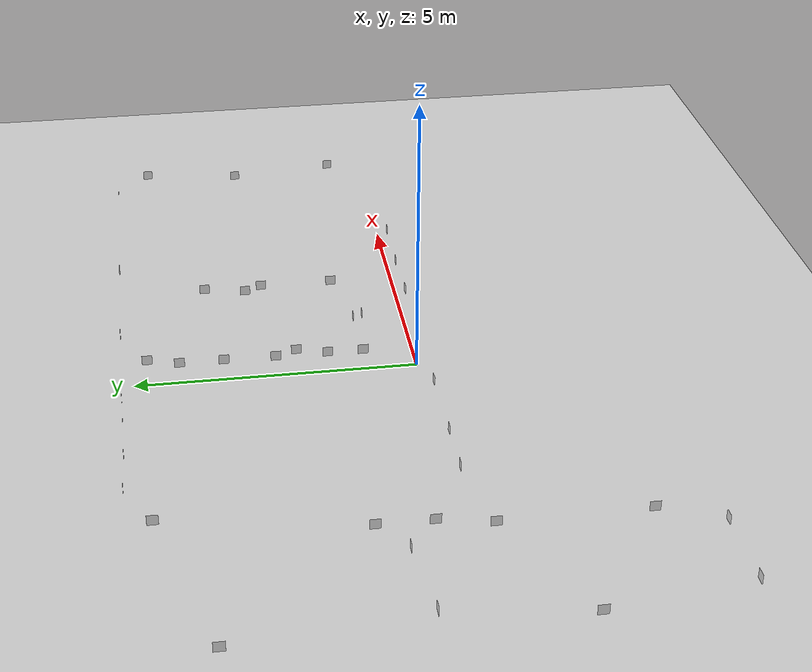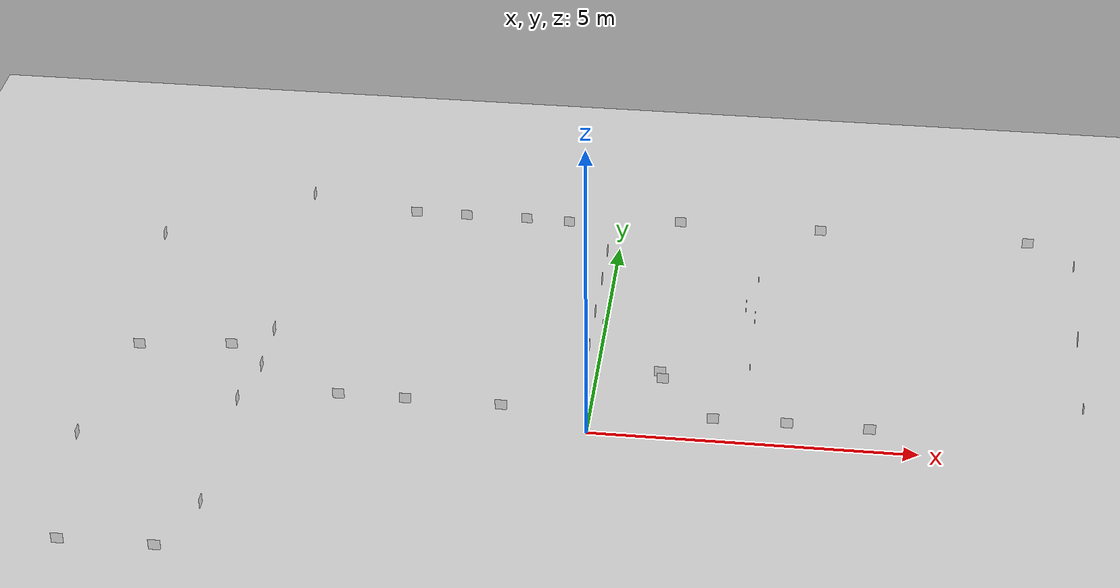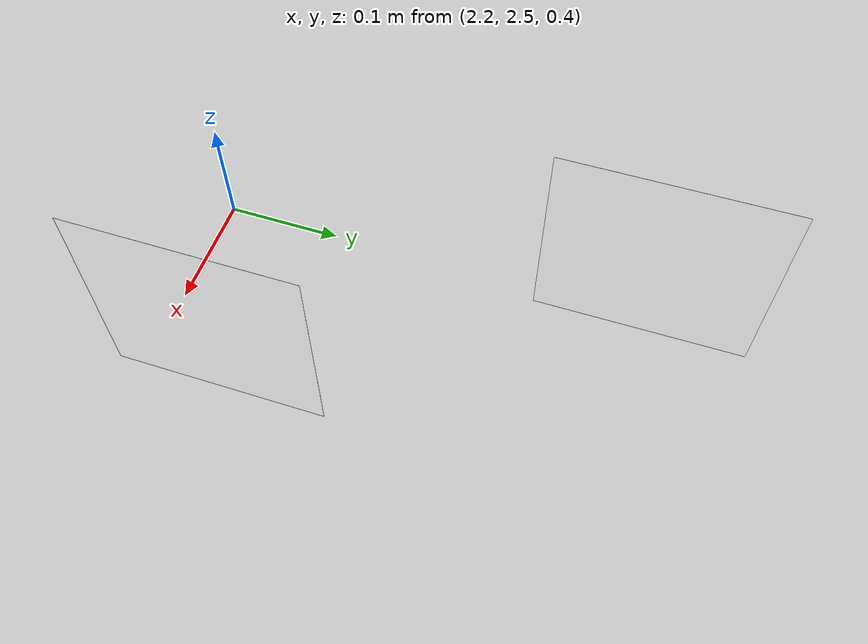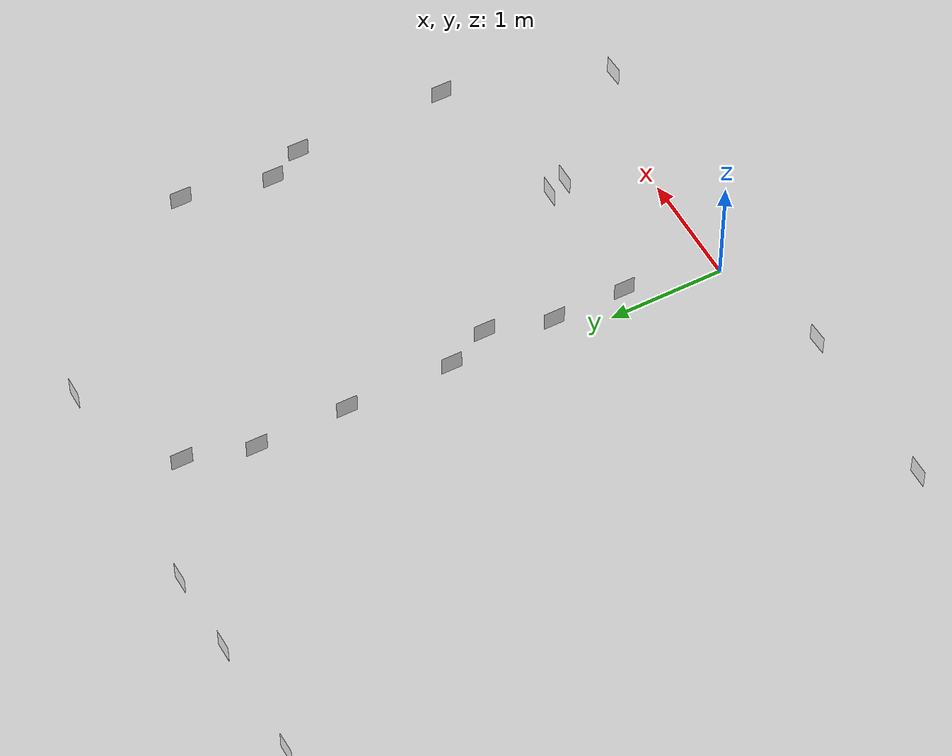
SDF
<sdf version="1.6">
 <world name="default">
  <light name="sun" type="directional">
   <pose>0 0 10 0 -0 0</pose>
   <diffuse>0.8 0.8 0.8 1</diffuse>
   <specular>0.2 0.2 0.2 1</specular>
   <attenuation>
    <range>1000</range>
    <constant>0.9</constant>
    <linear>0.01</linear>
    <quadratic>0.001</quadratic>
   </attenuation>
   <direction>-0.5 0.1 -0.9</direction>
  </light>
  <model name="ground_plane">
   <static>1</static>
   <link name="link">
    <collision name="collision">
     <geometry><plane><normal>0 0 1</normal><size>100 100</size></plane></geometry>
     <surface>
      <contact><collide_bitmask>65535</collide_bitmask></contact>
      <friction><ode><mu>100</mu><mu2>50</mu2></ode></friction>
     </surface>
    </collision>
    <visual name="visual">
     <cast_shadows>0</cast_shadows>
     <geometry><plane><normal>0 0 1</normal><size>100 100</size></plane></geometry>
     <material>
      <script><uri>file://media/materials/scripts/gazebo.material</uri><name>Gazebo/Grey</name></script>
     </material>
    </visual>
   </link>
  </model>
  <physics name="default_physics" default="0" type="ode">
   <real_time_update_rate>1000</real_time_update_rate>
   <max_step_size>0.001</max_step_size>
   <real_time_factor>1</real_time_factor>
   <ode>
    <solver>
     <type>quick</type>
     <iters>150</iters>
     <precon_iters>0</precon_iters>
     <sor>1.4</sor>
     <use_dynamic_moi_rescaling>1</use_dynamic_moi_rescaling>
    </solver>
    <constraints>
     <cfm>1e-05</cfm>
     <erp>0.2</erp>
     <contact_max_correcting_vel>2000</contact_max_correcting_vel>
     <contact_surface_layer>0.01</contact_surface_layer>
    </constraints>
   </ode>
  </physics>
  <scene><ambient>0.4 0.4 0.4 1</ambient><background>0.7 0.7 0.7 1</background><shadows>1</shadows></scene>
  <gravity>0 0 -9.8</gravity>
  <magnetic_field>6e-06 2.3e-05 -4.2e-05</magnetic_field>
  <atmosphere type="adiabatic"/>
  <spherical_coordinates>
   <surface_model>EARTH_WGS84</surface_model>
   <latitude_deg>0</latitude_deg>
   <longitude_deg>0</longitude_deg>
   <elevation>0</elevation>
   <heading_deg>0</heading_deg>
  </spherical_coordinates>
  <model name="marker_0">
   <link name="marker">
    <pose>0 0 0.5 3.14159 1.57079 3.14159</pose>
    <visual name="visual">
     <geometry><box><size>0.1778 0.1778 1e-05</size></box></geometry>
     <material>
      <script>
       <uri>model://marker_0/materials/scripts</uri>
       <uri>model://marker_0/materials/textures</uri>
       <name>Marker0/Marker</name>
      </script>
      <ambient>1 1 1 1</ambient>
      <diffuse>1 1 1 1</diffuse>
      <specular>0 0 0 1</specular>
      <emissive>1 1 1 0</emissive>
      <shader type="vertex"><normal_map>__default__</normal_map></shader>
     </material>
    </visual>
    <collision name="collision"><geometry><box><size>0.1778 0.1778 1e-05</size></box></geometry></collision>
   </link>
   <link name="marker_pad">
    <pose frame="marker">0 0 -1e-05 0 -0 0</pose>
    <visual name="visual">
     <geometry><box><size>0.1778 0.1778 1e-05</size></box></geometry>
     <material>
      <lighting>1</lighting>
      <script><uri>file://media/materials/scripts/gazebo.material</uri><name>Gazebo/White</name></script>
      <ambient>0.3 0.3 0.3 1</ambient>
      <diffuse>0.7 0.7 0.7 1</diffuse>
      <specular>0.01 0.01 0.01 1</specular>
      <emissive>1 1 1 0</emissive>
      <shader type="vertex"><normal_map>__default__</normal_map></shader>
     </material>
    </visual>
    <collision name="collision"><geometry><box><size>0.1778 0.1778 1e-05</size></box></geometry></collision>
   </link>
   <joint name="marker_JOINT_marker_pad" type="revolute">
    <parent>marker</parent>
    <child>marker_pad</child>
    <axis>
     <xyz>0 0 1</xyz>
     <limit><upper>0</upper><lower>0</lower></limit>
     <use_parent_model_frame>0</use_parent_model_frame>
     <dynamics><spring_reference>0</spring_reference><spring_stiffness>0</spring_stiffness></dynamics>
    </axis>
   </joint>
   <static>1</static>
   <pose>-5.06798 1.45437 -0 0 -0 0</pose>
  </model>
  <model name="marker_1">
   <link name="marker">
    <pose>0 0 0.5 3.14159 1.57079 3.14159</pose>
    <visual name="visual">
     <geometry><box><size>0.1778 0.1778 1e-05</size></box></geometry>
     <material>
      <script>
       <uri>model://marker_1/materials/scripts</uri>
       <uri>model://marker_1/materials/textures</uri>
       <name>Marker1/Marker</name>
      </script>
      <ambient>1 1 1 1</ambient>
      <diffuse>1 1 1 1</diffuse>
      <specular>0 0 0 1</specular>
      <emissive>1 1 1 0</emissive>
      <shader type="vertex"><normal_map>__default__</normal_map></shader>
     </material>
    </visual>
    <collision name="collision"><geometry><box><size>0.1778 0.1778 1e-05</size></box></geometry></collision>
   </link>
   <link name="marker_pad">
    <pose frame="marker">0 0 -1e-05 0 -0 0</pose>
    <visual name="visual">
     <geometry><box><size>0.1778 0.1778 1e-05</size></box></geometry>
     <material>
      <lighting>1</lighting>
      <script><uri>file://media/materials/scripts/gazebo.material</uri><name>Gazebo/White</name></script>
      <ambient>0.3 0.3 0.3 1</ambient>
      <diffuse>0.7 0.7 0.7 1</diffuse>
      <specular>0.01 0.01 0.01 1</specular>
      <emissive>1 1 1 0</emissive>
      <shader type="vertex"><normal_map>__default__</normal_map></shader>
     </material>
    </visual>
    <collision name="collision"><geometry><box><size>0.1778 0.1778 1e-05</size></box></geometry></collision>
   </link>
   <joint name="marker_JOINT_marker_pad" type="revolute">
    <parent>marker</parent>
    <child>marker_pad</child>
    <axis>
     <xyz>0 0 1</xyz>
     <limit><upper>0</upper><lower>0</lower></limit>
     <use_parent_model_frame>0</use_parent_model_frame>
     <dynamics><spring_reference>0</spring_reference><spring_stiffness>0</spring_stiffness></dynamics>
    </axis>
   </joint>
   <static>1</static>
   <pose>-5.06975 0.53307 -0 0 -0 0</pose>
  </model>
  <model name="marker_2">
   <link name="marker">
    <pose>0 0 0.5 3.14159 1.57079 3.14159</pose>
    <visual name="visual">
     <geometry><box><size>0.1778 0.1778 1e-05</size></box></geometry>
     <material>
      <script>
       <uri>model://marker_2/materials/scripts</uri>
       <uri>model://marker_2/materials/textures</uri>
       <name>Marker2/Marker</name>
      </script>
      <ambient>1 1 1 1</ambient>
      <diffuse>1 1 1 1</diffuse>
      <specular>0 0 0 1</specular>
      <emissive>1 1 1 0</emissive>
      <shader type="vertex"><normal_map>__default__</normal_map></shader>
     </material>
    </visual>
    <collision name="collision"><geometry><box><size>0.1778 0.1778 1e-05</size></box></geometry></collision>
   </link>
   <link name="marker_pad">
    <pose frame="marker">0 0 -1e-05 0 -0 0</pose>
    <visual name="visual">
     <geometry><box><size>0.1778 0.1778 1e-05</size></box></geometry>
     <material>
      <lighting>1</lighting>
      <script><uri>file://media/materials/scripts/gazebo.material</uri><name>Gazebo/White</name></script>
      <ambient>0.3 0.3 0.3 1</ambient>
      <diffuse>0.7 0.7 0.7 1</diffuse>
      <specular>0.01 0.01 0.01 1</specular>
      <emissive>1 1 1 0</emissive>
      <shader type="vertex"><normal_map>__default__</normal_map></shader>
     </material>
    </visual>
    <collision name="collision"><geometry><box><size>0.1778 0.1778 1e-05</size></box></geometry></collision>
   </link>
   <joint name="marker_JOINT_marker_pad" type="revolute">
    <parent>marker</parent>
    <child>marker_pad</child>
    <axis>
     <xyz>0 0 1</xyz>
     <limit><upper>0</upper><lower>0</lower></limit>
     <use_parent_model_frame>0</use_parent_model_frame>
     <dynamics><spring_reference>0</spring_reference><spring_stiffness>0</spring_stiffness></dynamics>
    </axis>
   </joint>
   <static>1</static>
   <pose>-5.04756 4.73456 0.419264 0 -0 0</pose>
  </model>
  <model name="marker_3">
   <link name="marker">
    <pose>0 0 0.5 3.14159 1.57079 3.14159</pose>
    <visual name="visual">
     <geometry><box><size>0.1778 0.1778 1e-05</size></box></geometry>
     <material>
      <script>
       <uri>model://marker_3/materials/scripts</uri>
       <uri>model://marker_3/materials/textures</uri>
       <name>Marker3/Marker</name>
      </script>
      <ambient>1 1 1 1</ambient>
      <diffuse>1 1 1 1</diffuse>
      <specular>0 0 0 1</specular>
      <emissive>1 1 1 0</emissive>
      <shader type="vertex"><normal_map>__default__</normal_map></shader>
     </material>
    </visual>
    <collision name="collision"><geometry><box><size>0.1778 0.1778 1e-05</size></box></geometry></collision>
   </link>
   <link name="marker_pad">
    <pose frame="marker">0 0 -1e-05 0 -0 0</pose>
    <visual name="visual">
     <geometry><box><size>0.1778 0.1778 1e-05</size></box></geometry>
     <material>
      <lighting>1</lighting>
      <script><uri>file://media/materials/scripts/gazebo.material</uri><name>Gazebo/White</name></script>
      <ambient>0.3 0.3 0.3 1</ambient>
      <diffuse>0.7 0.7 0.7 1</diffuse>
      <specular>0.01 0.01 0.01 1</specular>
      <emissive>1 1 1 0</emissive>
      <shader type="vertex"><normal_map>__default__</normal_map></shader>
     </material>
    </visual>
    <collision name="collision"><geometry><box><size>0.1778 0.1778 1e-05</size></box></geometry></collision>
   </link>
   <joint name="marker_JOINT_marker_pad" type="revolute">
    <parent>marker</parent>
    <child>marker_pad</child>
    <axis>
     <xyz>0 0 1</xyz>
     <limit><upper>0</upper><lower>0</lower></limit>
     <use_parent_model_frame>0</use_parent_model_frame>
     <dynamics><spring_reference>0</spring_reference><spring_stiffness>0</spring_stiffness></dynamics>
    </axis>
   </joint>
   <static>1</static>
   <pose>-3.75776 -0.082872 0 -0 -0 -1.57218</pose>
  </model>
  <model name="marker_4">
   <link name="marker">
    <pose>0 0 0.5 3.14159 1.57079 3.14159</pose>
    <visual name="visual">
     <geometry><box><size>0.1778 0.1778 1e-05</size></box></geometry>
     <material>
      <script>
       <uri>model://marker_4/materials/scripts</uri>
       <uri>model://marker_4/materials/textures</uri>
       <name>Marker4/Marker</name>
      </script>
      <ambient>1 1 1 1</ambient>
      <diffuse>1 1 1 1</diffuse>
      <specular>0 0 0 1</specular>
      <emissive>1 1 1 0</emissive>
      <shader type="vertex"><normal_map>__default__</normal_map></shader>
     </material>
    </visual>
    <collision name="collision"><geometry><box><size>0.1778 0.1778 1e-05</size></box></geometry></collision>
   </link>
   <link name="marker_pad">
    <pose frame="marker">0 0 -1e-05 0 -0 0</pose>
    <visual name="visual">
     <geometry><box><size>0.1778 0.1778 1e-05</size></box></geometry>
     <material>
      <lighting>1</lighting>
      <script><uri>file://media/materials/scripts/gazebo.material</uri><name>Gazebo/White</name></script>
      <ambient>0.3 0.3 0.3 1</ambient>
      <diffuse>0.7 0.7 0.7 1</diffuse>
      <specular>0.01 0.01 0.01 1</specular>
      <emissive>1 1 1 0</emissive>
      <shader type="vertex"><normal_map>__default__</normal_map></shader>
     </material>
    </visual>
    <collision name="collision"><geometry><box><size>0.1778 0.1778 1e-05</size></box></geometry></collision>
   </link>
   <joint name="marker_JOINT_marker_pad" type="revolute">
    <parent>marker</parent>
    <child>marker_pad</child>
    <axis>
     <xyz>0 0 1</xyz>
     <limit><upper>0</upper><lower>0</lower></limit>
     <use_parent_model_frame>0</use_parent_model_frame>
     <dynamics><spring_reference>0</spring_reference><spring_stiffness>0</spring_stiffness></dynamics>
    </axis>
   </joint>
   <static>1</static>
   <pose>-2.73633 -0.08731 0 0 0 -1.57853</pose>
  </model>
  <model name="marker_5">
   <link name="marker">
    <pose>0 0 0.5 3.14159 1.57079 3.14159</pose>
    <visual name="visual">
     <geometry><box><size>0.1778 0.1778 1e-05</size></box></geometry>
     <material>
      <script>
       <uri>model://marker_5/materials/scripts</uri>
       <uri>model://marker_5/materials/textures</uri>
       <name>Marker5/Marker</name>
      </script>
      <ambient>1 1 1 1</ambient>
      <diffuse>1 1 1 1</diffuse>
      <specular>0 0 0 1</specular>
      <emissive>1 1 1 0</emissive>
      <shader type="vertex"><normal_map>__default__</normal_map></shader>
     </material>
    </visual>
    <collision name="collision"><geometry><box><size>0.1778 0.1778 1e-05</size></box></geometry></collision>
   </link>
   <link name="marker_pad">
    <pose frame="marker">0 0 -1e-05 0 -0 0</pose>
    <visual name="visual">
     <geometry><box><size>0.1778 0.1778 1e-05</size></box></geometry>
     <material>
      <lighting>1</lighting>
      <script><uri>file://media/materials/scripts/gazebo.material</uri><name>Gazebo/White</name></script>
      <ambient>0.3 0.3 0.3 1</ambient>
      <diffuse>0.7 0.7 0.7 1</diffuse>
      <specular>0.01 0.01 0.01 1</specular>
      <emissive>1 1 1 0</emissive>
      <shader type="vertex"><normal_map>__default__</normal_map></shader>
     </material>
    </visual>
    <collision name="collision"><geometry><box><size>0.1778 0.1778 1e-05</size></box></geometry></collision>
   </link>
   <joint name="marker_JOINT_marker_pad" type="revolute">
    <parent>marker</parent>
    <child>marker_pad</child>
    <axis>
     <xyz>0 0 1</xyz>
     <limit><upper>0</upper><lower>0</lower></limit>
     <use_parent_model_frame>0</use_parent_model_frame>
     <dynamics><spring_reference>0</spring_reference><spring_stiffness>0</spring_stiffness></dynamics>
    </axis>
   </joint>
   <static>1</static>
   <pose>-1.27819 -0.089903 0 -0 -0 -1.53704</pose>
  </model>
  <model name="marker_6">
   <link name="marker">
    <pose>0 0 0.5 3.14159 1.57079 3.14159</pose>
    <visual name="visual">
     <geometry><box><size>0.1778 0.1778 1e-05</size></box></geometry>
     <material>
      <script>
       <uri>model://marker_6/materials/scripts</uri>
       <uri>model://marker_6/materials/textures</uri>
       <name>Marker6/Marker</name>
      </script>
      <ambient>1 1 1 1</ambient>
      <diffuse>1 1 1 1</diffuse>
      <specular>0 0 0 1</specular>
      <emissive>1 1 1 0</emissive>
      <shader type="vertex"><normal_map>__default__</normal_map></shader>
     </material>
    </visual>
    <collision name="collision"><geometry><box><size>0.1778 0.1778 1e-05</size></box></geometry></collision>
   </link>
   <link name="marker_pad">
    <pose frame="marker">0 0 -1e-05 0 -0 0</pose>
    <visual name="visual">
     <geometry><box><size>0.1778 0.1778 1e-05</size></box></geometry>
     <material>
      <lighting>1</lighting>
      <script><uri>file://media/materials/scripts/gazebo.material</uri><name>Gazebo/White</name></script>
      <ambient>0.3 0.3 0.3 1</ambient>
      <diffuse>0.7 0.7 0.7 1</diffuse>
      <specular>0.01 0.01 0.01 1</specular>
      <emissive>1 1 1 0</emissive>
      <shader type="vertex"><normal_map>__default__</normal_map></shader>
     </material>
    </visual>
    <collision name="collision"><geometry><box><size>0.1778 0.1778 1e-05</size></box></geometry></collision>
   </link>
   <joint name="marker_JOINT_marker_pad" type="revolute">
    <parent>marker</parent>
    <child>marker_pad</child>
    <axis>
     <xyz>0 0 1</xyz>
     <limit><upper>0</upper><lower>0</lower></limit>
     <use_parent_model_frame>0</use_parent_model_frame>
     <dynamics><spring_reference>0</spring_reference><spring_stiffness>0</spring_stiffness></dynamics>
    </axis>
   </joint>
   <static>1</static>
   <pose>-0.129222 1.60005 -0 0 -0 0</pose>
  </model>
  <model name="marker_7">
   <link name="marker">
    <pose>0 0 0.5 3.14159 1.57079 3.14159</pose>
    <visual name="visual">
     <geometry><box><size>0.1778 0.1778 1e-05</size></box></geometry>
     <material>
      <script>
       <uri>model://marker_7/materials/scripts</uri>
       <uri>model://marker_7/materials/textures</uri>
       <name>Marker7/Marker</name>
      </script>
      <ambient>1 1 1 1</ambient>
      <diffuse>1 1 1 1</diffuse>
      <specular>0 0 0 1</specular>
      <emissive>1 1 1 0</emissive>
      <shader type="vertex"><normal_map>__default__</normal_map></shader>
     </material>
    </visual>
    <collision name="collision"><geometry><box><size>0.1778 0.1778 1e-05</size></box></geometry></collision>
   </link>
   <link name="marker_pad">
    <pose frame="marker">0 0 -1e-05 0 -0 0</pose>
    <visual name="visual">
     <geometry><box><size>0.1778 0.1778 1e-05</size></box></geometry>
     <material>
      <lighting>1</lighting>
      <script><uri>file://media/materials/scripts/gazebo.material</uri><name>Gazebo/White</name></script>
      <ambient>0.3 0.3 0.3 1</ambient>
      <diffuse>0.7 0.7 0.7 1</diffuse>
      <specular>0.01 0.01 0.01 1</specular>
      <emissive>1 1 1 0</emissive>
      <shader type="vertex"><normal_map>__default__</normal_map></shader>
     </material>
    </visual>
    <collision name="collision"><geometry><box><size>0.1778 0.1778 1e-05</size></box></geometry></collision>
   </link>
   <joint name="marker_JOINT_marker_pad" type="revolute">
    <parent>marker</parent>
    <child>marker_pad</child>
    <axis>
     <xyz>0 0 1</xyz>
     <limit><upper>0</upper><lower>0</lower></limit>
     <use_parent_model_frame>0</use_parent_model_frame>
     <dynamics><spring_reference>0</spring_reference><spring_stiffness>0</spring_stiffness></dynamics>
    </axis>
   </joint>
   <static>1</static>
   <pose>-0.131428 0.975175 -0 0 -0 0</pose>
  </model>
  <model name="marker_8">
   <link name="marker">
    <pose>0 0 0.5 3.14159 1.57079 3.14159</pose>
    <visual name="visual">
     <geometry><box><size>0.1778 0.1778 1e-05</size></box></geometry>
     <material>
      <script>
       <uri>model://marker_8/materials/scripts</uri>
       <uri>model://marker_8/materials/textures</uri>
       <name>Marker8/Marker</name>
      </script>
      <ambient>1 1 1 1</ambient>
      <diffuse>1 1 1 1</diffuse>
      <specular>0 0 0 1</specular>
      <emissive>1 1 1 0</emissive>
      <shader type="vertex"><normal_map>__default__</normal_map></shader>
     </material>
    </visual>
    <collision name="collision"><geometry><box><size>0.1778 0.1778 1e-05</size></box></geometry></collision>
   </link>
   <link name="marker_pad">
    <pose frame="marker">0 0 -1e-05 0 -0 0</pose>
    <visual name="visual">
     <geometry><box><size>0.1778 0.1778 1e-05</size></box></geometry>
     <material>
      <lighting>1</lighting>
      <script><uri>file://media/materials/scripts/gazebo.material</uri><name>Gazebo/White</name></script>
      <ambient>0.3 0.3 0.3 1</ambient>
      <diffuse>0.7 0.7 0.7 1</diffuse>
      <specular>0.01 0.01 0.01 1</specular>
      <emissive>1 1 1 0</emissive>
      <shader type="vertex"><normal_map>__default__</normal_map></shader>
     </material>
    </visual>
    <collision name="collision"><geometry><box><size>0.1778 0.1778 1e-05</size></box></geometry></collision>
   </link>
   <joint name="marker_JOINT_marker_pad" type="revolute">
    <parent>marker</parent>
    <child>marker_pad</child>
    <axis>
     <xyz>0 0 1</xyz>
     <limit><upper>0</upper><lower>0</lower></limit>
     <use_parent_model_frame>0</use_parent_model_frame>
     <dynamics><spring_reference>0</spring_reference><spring_stiffness>0</spring_stiffness></dynamics>
    </axis>
   </joint>
   <static>1</static>
   <pose>-0.136663 2.51024 -0 0 -0 0</pose>
  </model>
  <model name="marker_9">
   <link name="marker">
    <pose>0 0 0.5 3.14159 1.57079 3.14159</pose>
    <visual name="visual">
     <geometry><box><size>0.1778 0.1778 1e-05</size></box></geometry>
     <material>
      <script>
       <uri>model://marker_9/materials/scripts</uri>
       <uri>model://marker_9/materials/textures</uri>
       <name>Marker9/Marker</name>
      </script>
      <ambient>1 1 1 1</ambient>
      <diffuse>1 1 1 1</diffuse>
      <specular>0 0 0 1</specular>
      <emissive>1 1 1 0</emissive>
      <shader type="vertex"><normal_map>__default__</normal_map></shader>
     </material>
    </visual>
    <collision name="collision"><geometry><box><size>0.1778 0.1778 1e-05</size></box></geometry></collision>
   </link>
   <link name="marker_pad">
    <pose frame="marker">0 0 -1e-05 0 -0 0</pose>
    <visual name="visual">
     <geometry><box><size>0.1778 0.1778 1e-05</size></box></geometry>
     <material>
      <lighting>1</lighting>
      <script><uri>file://media/materials/scripts/gazebo.material</uri><name>Gazebo/White</name></script>
      <ambient>0.3 0.3 0.3 1</ambient>
      <diffuse>0.7 0.7 0.7 1</diffuse>
      <specular>0.01 0.01 0.01 1</specular>
      <emissive>1 1 1 0</emissive>
      <shader type="vertex"><normal_map>__default__</normal_map></shader>
     </material>
    </visual>
    <collision name="collision"><geometry><box><size>0.1778 0.1778 1e-05</size></box></geometry></collision>
   </link>
   <joint name="marker_JOINT_marker_pad" type="revolute">
    <parent>marker</parent>
    <child>marker_pad</child>
    <axis>
     <xyz>0 0 1</xyz>
     <limit><upper>0</upper><lower>0</lower></limit>
     <use_parent_model_frame>0</use_parent_model_frame>
     <dynamics><spring_reference>0</spring_reference><spring_stiffness>0</spring_stiffness></dynamics>
    </axis>
   </joint>
   <static>1</static>
   <pose>-0.127555 3.41147 -0 0 -0 0</pose>
  </model>
  <model name="marker_10">
   <link name="marker">
    <pose>0 0 0.5 3.14159 1.57079 3.14159</pose>
    <visual name="visual">
     <geometry><box><size>0.1778 0.1778 1e-05</size></box></geometry>
     <material>
      <script>
       <uri>model://marker_10/materials/scripts</uri>
       <uri>model://marker_10/materials/textures</uri>
       <name>Marker10/Marker</name>
      </script>
      <ambient>1 1 1 1</ambient>
      <diffuse>1 1 1 1</diffuse>
      <specular>0 0 0 1</specular>
      <emissive>1 1 1 0</emissive>
      <shader type="vertex"><normal_map>__default__</normal_map></shader>
     </material>
    </visual>
    <collision name="collision"><geometry><box><size>0.1778 0.1778 1e-05</size></box></geometry></collision>
   </link>
   <link name="marker_pad">
    <pose frame="marker">0 0 -1e-05 0 -0 0</pose>
    <visual name="visual">
     <geometry><box><size>0.1778 0.1778 1e-05</size></box></geometry>
     <material>
      <lighting>1</lighting>
      <script><uri>file://media/materials/scripts/gazebo.material</uri><name>Gazebo/White</name></script>
      <ambient>0.3 0.3 0.3 1</ambient>
      <diffuse>0.7 0.7 0.7 1</diffuse>
      <specular>0.01 0.01 0.01 1</specular>
      <emissive>1 1 1 0</emissive>
      <shader type="vertex"><normal_map>__default__</normal_map></shader>
     </material>
    </visual>
    <collision name="collision"><geometry><box><size>0.1778 0.1778 1e-05</size></box></geometry></collision>
   </link>
   <joint name="marker_JOINT_marker_pad" type="revolute">
    <parent>marker</parent>
    <child>marker_pad</child>
    <axis>
     <xyz>0 0 1</xyz>
     <limit><upper>0</upper><lower>0</lower></limit>
     <use_parent_model_frame>0</use_parent_model_frame>
     <dynamics><spring_reference>0</spring_reference><spring_stiffness>0</spring_stiffness></dynamics>
    </axis>
   </joint>
   <static>1</static>
   <pose>-0.12839 4.18068 -0 0 -0 0</pose>
  </model>
  <model name="marker_11">
   <link name="marker">
    <pose>0 0 0.5 3.14159 1.57079 3.14159</pose>
    <visual name="visual">
     <geometry><box><size>0.1778 0.1778 1e-05</size></box></geometry>
     <material>
      <script>
       <uri>model://marker_11/materials/scripts</uri>
       <uri>model://marker_11/materials/textures</uri>
       <name>Marker11/Marker</name>
      </script>
      <ambient>1 1 1 1</ambient>
      <diffuse>1 1 1 1</diffuse>
      <specular>0 0 0 1</specular>
      <emissive>1 1 1 0</emissive>
      <shader type="vertex"><normal_map>__default__</normal_map></shader>
     </material>
    </visual>
    <collision name="collision"><geometry><box><size>0.1778 0.1778 1e-05</size></box></geometry></collision>
   </link>
   <link name="marker_pad">
    <pose frame="marker">0 0 -1e-05 0 -0 0</pose>
    <visual name="visual">
     <geometry><box><size>0.1778 0.1778 1e-05</size></box></geometry>
     <material>
      <lighting>1</lighting>
      <script><uri>file://media/materials/scripts/gazebo.material</uri><name>Gazebo/White</name></script>
      <ambient>0.3 0.3 0.3 1</ambient>
      <diffuse>0.7 0.7 0.7 1</diffuse>
      <specular>0.01 0.01 0.01 1</specular>
      <emissive>1 1 1 0</emissive>
      <shader type="vertex"><normal_map>__default__</normal_map></shader>
     </material>
    </visual>
    <collision name="collision"><geometry><box><size>0.1778 0.1778 1e-05</size></box></geometry></collision>
   </link>
   <joint name="marker_JOINT_marker_pad" type="revolute">
    <parent>marker</parent>
    <child>marker_pad</child>
    <axis>
     <xyz>0 0 1</xyz>
     <limit><upper>0</upper><lower>0</lower></limit>
     <use_parent_model_frame>0</use_parent_model_frame>
     <dynamics><spring_reference>0</spring_reference><spring_stiffness>0</spring_stiffness></dynamics>
    </axis>
   </joint>
   <static>1</static>
   <pose>-0.872853 5.19289 -0.125133 0 0 -1.55002</pose>
  </model>
  <model name="marker_12">
   <link name="marker">
    <pose>0 0 0.5 3.14159 1.57079 3.14159</pose>
    <visual name="visual">
     <geometry><box><size>0.1778 0.1778 1e-05</size></box></geometry>
     <material>
      <script>
       <uri>model://marker_12/materials/scripts</uri>
       <uri>model://marker_12/materials/textures</uri>
       <name>Marker12/Marker</name>
      </script>
      <ambient>1 1 1 1</ambient>
      <diffuse>1 1 1 1</diffuse>
      <specular>0 0 0 1</specular>
      <emissive>1 1 1 0</emissive>
      <shader type="vertex"><normal_map>__default__</normal_map></shader>
     </material>
    </visual>
    <collision name="collision"><geometry><box><size>0.1778 0.1778 1e-05</size></box></geometry></collision>
   </link>
   <link name="marker_pad">
    <pose frame="marker">0 0 -1e-05 0 -0 0</pose>
    <visual name="visual">
     <geometry><box><size>0.1778 0.1778 1e-05</size></box></geometry>
     <material>
      <lighting>1</lighting>
      <script><uri>file://media/materials/scripts/gazebo.material</uri><name>Gazebo/White</name></script>
      <ambient>0.3 0.3 0.3 1</ambient>
      <diffuse>0.7 0.7 0.7 1</diffuse>
      <specular>0.01 0.01 0.01 1</specular>
      <emissive>1 1 1 0</emissive>
      <shader type="vertex"><normal_map>__default__</normal_map></shader>
     </material>
    </visual>
    <collision name="collision"><geometry><box><size>0.1778 0.1778 1e-05</size></box></geometry></collision>
   </link>
   <joint name="marker_JOINT_marker_pad" type="revolute">
    <parent>marker</parent>
    <child>marker_pad</child>
    <axis>
     <xyz>0 0 1</xyz>
     <limit><upper>0</upper><lower>0</lower></limit>
     <use_parent_model_frame>0</use_parent_model_frame>
     <dynamics><spring_reference>0</spring_reference><spring_stiffness>0</spring_stiffness></dynamics>
    </axis>
   </joint>
   <static>1</static>
   <pose>-1.58601 5.18065 -0.099927 0 0 -1.55991</pose>
  </model>
  <model name="marker_13">
   <link name="marker">
    <pose>0 0 0.5 3.14159 1.57079 3.14159</pose>
    <visual name="visual">
     <geometry><box><size>0.1778 0.1778 1e-05</size></box></geometry>
     <material>
      <script>
       <uri>model://marker_13/materials/scripts</uri>
       <uri>model://marker_13/materials/textures</uri>
       <name>Marker13/Marker</name>
      </script>
      <ambient>1 1 1 1</ambient>
      <diffuse>1 1 1 1</diffuse>
      <specular>0 0 0 1</specular>
      <emissive>1 1 1 0</emissive>
      <shader type="vertex"><normal_map>__default__</normal_map></shader>
     </material>
    </visual>
    <collision name="collision"><geometry><box><size>0.1778 0.1778 1e-05</size></box></geometry></collision>
   </link>
   <link name="marker_pad">
    <pose frame="marker">0 0 -1e-05 0 -0 0</pose>
    <visual name="visual">
     <geometry><box><size>0.1778 0.1778 1e-05</size></box></geometry>
     <material>
      <lighting>1</lighting>
      <script><uri>file://media/materials/scripts/gazebo.material</uri><name>Gazebo/White</name></script>
      <ambient>0.3 0.3 0.3 1</ambient>
      <diffuse>0.7 0.7 0.7 1</diffuse>
      <specular>0.01 0.01 0.01 1</specular>
      <emissive>1 1 1 0</emissive>
      <shader type="vertex"><normal_map>__default__</normal_map></shader>
     </material>
    </visual>
    <collision name="collision"><geometry><box><size>0.1778 0.1778 1e-05</size></box></geometry></collision>
   </link>
   <joint name="marker_JOINT_marker_pad" type="revolute">
    <parent>marker</parent>
    <child>marker_pad</child>
    <axis>
     <xyz>0 0 1</xyz>
     <limit><upper>0</upper><lower>0</lower></limit>
     <use_parent_model_frame>0</use_parent_model_frame>
     <dynamics><spring_reference>0</spring_reference><spring_stiffness>0</spring_stiffness></dynamics>
    </axis>
   </joint>
   <static>1</static>
   <pose>-2.5968 5.17229 -0.09997 0 0 -1.55268</pose>
  </model>
  <model name="marker_14">
   <link name="marker">
    <pose>0 0 0.5 3.14159 1.57079 3.14159</pose>
    <visual name="visual">
     <geometry><box><size>0.1778 0.1778 1e-05</size></box></geometry>
     <material>
      <script>
       <uri>model://marker_14/materials/scripts</uri>
       <uri>model://marker_14/materials/textures</uri>
       <name>Marker14/Marker</name>
      </script>
      <ambient>1 1 1 1</ambient>
      <diffuse>1 1 1 1</diffuse>
      <specular>0 0 0 1</specular>
      <emissive>1 1 1 0</emissive>
      <shader type="vertex"><normal_map>__default__</normal_map></shader>
     </material>
    </visual>
    <collision name="collision"><geometry><box><size>0.1778 0.1778 1e-05</size></box></geometry></collision>
   </link>
   <link name="marker_pad">
    <pose frame="marker">0 0 -1e-05 0 -0 0</pose>
    <visual name="visual">
     <geometry><box><size>0.1778 0.1778 1e-05</size></box></geometry>
     <material>
      <lighting>1</lighting>
      <script><uri>file://media/materials/scripts/gazebo.material</uri><name>Gazebo/White</name></script>
      <ambient>0.3 0.3 0.3 1</ambient>
      <diffuse>0.7 0.7 0.7 1</diffuse>
      <specular>0.01 0.01 0.01 1</specular>
      <emissive>1 1 1 0</emissive>
      <shader type="vertex"><normal_map>__default__</normal_map></shader>
     </material>
    </visual>
    <collision name="collision"><geometry><box><size>0.1778 0.1778 1e-05</size></box></geometry></collision>
   </link>
   <joint name="marker_JOINT_marker_pad" type="revolute">
    <parent>marker</parent>
    <child>marker_pad</child>
    <axis>
     <xyz>0 0 1</xyz>
     <limit><upper>0</upper><lower>0</lower></limit>
     <use_parent_model_frame>0</use_parent_model_frame>
     <dynamics><spring_reference>0</spring_reference><spring_stiffness>0</spring_stiffness></dynamics>
    </axis>
   </joint>
   <static>1</static>
   <pose>-3.44382 5.19355 -0.114165 -0 -0 -1.55778</pose>
  </model>
  <model name="marker_15">
   <link name="marker">
    <pose>0 0 0.5 3.14159 1.57079 3.14159</pose>
    <visual name="visual">
     <geometry><box><size>0.1778 0.1778 1e-05</size></box></geometry>
     <material>
      <script>
       <uri>model://marker_15/materials/scripts</uri>
       <uri>model://marker_15/materials/textures</uri>
       <name>Marker15/Marker</name>
      </script>
      <ambient>1 1 1 1</ambient>
      <diffuse>1 1 1 1</diffuse>
      <specular>0 0 0 1</specular>
      <emissive>1 1 1 0</emissive>
      <shader type="vertex"><normal_map>__default__</normal_map></shader>
     </material>
    </visual>
    <collision name="collision"><geometry><box><size>0.1778 0.1778 1e-05</size></box></geometry></collision>
   </link>
   <link name="marker_pad">
    <pose frame="marker">0 0 -1e-05 0 -0 0</pose>
    <visual name="visual">
     <geometry><box><size>0.1778 0.1778 1e-05</size></box></geometry>
     <material>
      <lighting>1</lighting>
      <script><uri>file://media/materials/scripts/gazebo.material</uri><name>Gazebo/White</name></script>
      <ambient>0.3 0.3 0.3 1</ambient>
      <diffuse>0.7 0.7 0.7 1</diffuse>
      <specular>0.01 0.01 0.01 1</specular>
      <emissive>1 1 1 0</emissive>
      <shader type="vertex"><normal_map>__default__</normal_map></shader>
     </material>
    </visual>
    <collision name="collision"><geometry><box><size>0.1778 0.1778 1e-05</size></box></geometry></collision>
   </link>
   <joint name="marker_JOINT_marker_pad" type="revolute">
    <parent>marker</parent>
    <child>marker_pad</child>
    <axis>
     <xyz>0 0 1</xyz>
     <limit><upper>0</upper><lower>0</lower></limit>
     <use_parent_model_frame>0</use_parent_model_frame>
     <dynamics><spring_reference>0</spring_reference><spring_stiffness>0</spring_stiffness></dynamics>
    </axis>
   </joint>
   <static>1</static>
   <pose>1.0762 0.836455 0 0 -0 -1.57179</pose>
  </model>
  <model name="marker_16">
   <link name="marker">
    <pose>0 0 0.5 3.14159 1.57079 3.14159</pose>
    <visual name="visual">
     <geometry><box><size>0.1778 0.1778 1e-05</size></box></geometry>
     <material>
      <script>
       <uri>model://marker_16/materials/scripts</uri>
       <uri>model://marker_16/materials/textures</uri>
       <name>Marker16/Marker</name>
      </script>
      <ambient>1 1 1 1</ambient>
      <diffuse>1 1 1 1</diffuse>
      <specular>0 0 0 1</specular>
      <emissive>1 1 1 0</emissive>
      <shader type="vertex"><normal_map>__default__</normal_map></shader>
     </material>
    </visual>
    <collision name="collision"><geometry><box><size>0.1778 0.1778 1e-05</size></box></geometry></collision>
   </link>
   <link name="marker_pad">
    <pose frame="marker">0 0 -1e-05 0 -0 0</pose>
    <visual name="visual">
     <geometry><box><size>0.1778 0.1778 1e-05</size></box></geometry>
     <material>
      <lighting>1</lighting>
      <script><uri>file://media/materials/scripts/gazebo.material</uri><name>Gazebo/White</name></script>
      <ambient>0.3 0.3 0.3 1</ambient>
      <diffuse>0.7 0.7 0.7 1</diffuse>
      <specular>0.01 0.01 0.01 1</specular>
      <emissive>1 1 1 0</emissive>
      <shader type="vertex"><normal_map>__default__</normal_map></shader>
     </material>
    </visual>
    <collision name="collision"><geometry><box><size>0.1778 0.1778 1e-05</size></box></geometry></collision>
   </link>
   <joint name="marker_JOINT_marker_pad" type="revolute">
    <parent>marker</parent>
    <child>marker_pad</child>
    <axis>
     <xyz>0 0 1</xyz>
     <limit><upper>0</upper><lower>0</lower></limit>
     <use_parent_model_frame>0</use_parent_model_frame>
     <dynamics><spring_reference>0</spring_reference><spring_stiffness>0</spring_stiffness></dynamics>
    </axis>
   </joint>
   <static>1</static>
   <pose>1.91062 -0.084933 -0 0 -0 -1.53266</pose>
  </model>
  <model name="marker_17">
   <link name="marker">
    <pose>0 0 0.5 3.14159 1.57079 3.14159</pose>
    <visual name="visual">
     <geometry><box><size>0.1778 0.1778 1e-05</size></box></geometry>
     <material>
      <script>
       <uri>model://marker_17/materials/scripts</uri>
       <uri>model://marker_17/materials/textures</uri>
       <name>Marker17/Marker</name>
      </script>
      <ambient>1 1 1 1</ambient>
      <diffuse>1 1 1 1</diffuse>
      <specular>0 0 0 1</specular>
      <emissive>1 1 1 0</emissive>
      <shader type="vertex"><normal_map>__default__</normal_map></shader>
     </material>
    </visual>
    <collision name="collision"><geometry><box><size>0.1778 0.1778 1e-05</size></box></geometry></collision>
   </link>
   <link name="marker_pad">
    <pose frame="marker">0 0 -1e-05 0 -0 0</pose>
    <visual name="visual">
     <geometry><box><size>0.1778 0.1778 1e-05</size></box></geometry>
     <material>
      <lighting>1</lighting>
      <script><uri>file://media/materials/scripts/gazebo.material</uri><name>Gazebo/White</name></script>
      <ambient>0.3 0.3 0.3 1</ambient>
      <diffuse>0.7 0.7 0.7 1</diffuse>
      <specular>0.01 0.01 0.01 1</specular>
      <emissive>1 1 1 0</emissive>
      <shader type="vertex"><normal_map>__default__</normal_map></shader>
     </material>
    </visual>
    <collision name="collision"><geometry><box><size>0.1778 0.1778 1e-05</size></box></geometry></collision>
   </link>
   <joint name="marker_JOINT_marker_pad" type="revolute">
    <parent>marker</parent>
    <child>marker_pad</child>
    <axis>
     <xyz>0 0 1</xyz>
     <limit><upper>0</upper><lower>0</lower></limit>
     <use_parent_model_frame>0</use_parent_model_frame>
     <dynamics><spring_reference>0</spring_reference><spring_stiffness>0</spring_stiffness></dynamics>
    </axis>
   </joint>
   <static>1</static>
   <pose>7.41019 0.749238 -0 0 -0 0</pose>
  </model>
  <model name="marker_18">
   <link name="marker">
    <pose>0 0 0.5 3.14159 1.57079 3.14159</pose>
    <visual name="visual">
     <geometry><box><size>0.1778 0.1778 1e-05</size></box></geometry>
     <material>
      <script>
       <uri>model://marker_18/materials/scripts</uri>
       <uri>model://marker_18/materials/textures</uri>
       <name>Marker18/Marker</name>
      </script>
      <ambient>1 1 1 1</ambient>
      <diffuse>1 1 1 1</diffuse>
      <specular>0 0 0 1</specular>
      <emissive>1 1 1 0</emissive>
      <shader type="vertex"><normal_map>__default__</normal_map></shader>
     </material>
    </visual>
    <collision name="collision"><geometry><box><size>0.1778 0.1778 1e-05</size></box></geometry></collision>
   </link>
   <link name="marker_pad">
    <pose frame="marker">0 0 -1e-05 0 -0 0</pose>
    <visual name="visual">
     <geometry><box><size>0.1778 0.1778 1e-05</size></box></geometry>
     <material>
      <lighting>1</lighting>
      <script><uri>file://media/materials/scripts/gazebo.material</uri><name>Gazebo/White</name></script>
      <ambient>0.3 0.3 0.3 1</ambient>
      <diffuse>0.7 0.7 0.7 1</diffuse>
      <specular>0.01 0.01 0.01 1</specular>
      <emissive>1 1 1 0</emissive>
      <shader type="vertex"><normal_map>__default__</normal_map></shader>
     </material>
    </visual>
    <collision name="collision"><geometry><box><size>0.1778 0.1778 1e-05</size></box></geometry></collision>
   </link>
   <joint name="marker_JOINT_marker_pad" type="revolute">
    <parent>marker</parent>
    <child>marker_pad</child>
    <axis>
     <xyz>0 0 1</xyz>
     <limit><upper>0</upper><lower>0</lower></limit>
     <use_parent_model_frame>0</use_parent_model_frame>
     <dynamics><spring_reference>0</spring_reference><spring_stiffness>0</spring_stiffness></dynamics>
    </axis>
   </joint>
   <static>1</static>
   <pose>4.24151 -0.092131 0 -0 -0 -1.55917</pose>
  </model>
  <model name="marker_19">
   <link name="marker">
    <pose>0 0 0.5 3.14159 1.57079 3.14159</pose>
    <visual name="visual">
     <geometry><box><size>0.1778 0.1778 1e-05</size></box></geometry>
     <material>
      <script>
       <uri>model://marker_19/materials/scripts</uri>
       <uri>model://marker_19/materials/textures</uri>
       <name>Marker19/Marker</name>
      </script>
      <ambient>1 1 1 1</ambient>
      <diffuse>1 1 1 1</diffuse>
      <specular>0 0 0 1</specular>
      <emissive>1 1 1 0</emissive>
      <shader type="vertex"><normal_map>__default__</normal_map></shader>
     </material>
    </visual>
    <collision name="collision"><geometry><box><size>0.1778 0.1778 1e-05</size></box></geometry></collision>
   </link>
   <link name="marker_pad">
    <pose frame="marker">0 0 -1e-05 0 -0 0</pose>
    <visual name="visual">
     <geometry><box><size>0.1778 0.1778 1e-05</size></box></geometry>
     <material>
      <lighting>1</lighting>
      <script><uri>file://media/materials/scripts/gazebo.material</uri><name>Gazebo/White</name></script>
      <ambient>0.3 0.3 0.3 1</ambient>
      <diffuse>0.7 0.7 0.7 1</diffuse>
      <specular>0.01 0.01 0.01 1</specular>
      <emissive>1 1 1 0</emissive>
      <shader type="vertex"><normal_map>__default__</normal_map></shader>
     </material>
    </visual>
    <collision name="collision"><geometry><box><size>0.1778 0.1778 1e-05</size></box></geometry></collision>
   </link>
   <joint name="marker_JOINT_marker_pad" type="revolute">
    <parent>marker</parent>
    <child>marker_pad</child>
    <axis>
     <xyz>0 0 1</xyz>
     <limit><upper>0</upper><lower>0</lower></limit>
     <use_parent_model_frame>0</use_parent_model_frame>
     <dynamics><spring_reference>0</spring_reference><spring_stiffness>0</spring_stiffness></dynamics>
    </axis>
   </joint>
   <static>1</static>
   <pose>3.29844 5.18401 0 -0 -0 -1.62154</pose>
  </model>
  <model name="marker_20">
   <link name="marker">
    <pose>0 0 0.5 3.14159 1.57079 3.14159</pose>
    <visual name="visual">
     <geometry><box><size>0.1778 0.1778 1e-05</size></box></geometry>
     <material>
      <script>
       <uri>model://marker_20/materials/scripts</uri>
       <uri>model://marker_20/materials/textures</uri>
       <name>Marker20/Marker</name>
      </script>
      <ambient>1 1 1 1</ambient>
      <diffuse>1 1 1 1</diffuse>
      <specular>0 0 0 1</specular>
      <emissive>1 1 1 0</emissive>
      <shader type="vertex"><normal_map>__default__</normal_map></shader>
     </material>
    </visual>
    <collision name="collision"><geometry><box><size>0.1778 0.1778 1e-05</size></box></geometry></collision>
   </link>
   <link name="marker_pad">
    <pose frame="marker">0 0 -1e-05 0 -0 0</pose>
    <visual name="visual">
     <geometry><box><size>0.1778 0.1778 1e-05</size></box></geometry>
     <material>
      <lighting>1</lighting>
      <script><uri>file://media/materials/scripts/gazebo.material</uri><name>Gazebo/White</name></script>
      <ambient>0.3 0.3 0.3 1</ambient>
      <diffuse>0.7 0.7 0.7 1</diffuse>
      <specular>0.01 0.01 0.01 1</specular>
      <emissive>1 1 1 0</emissive>
      <shader type="vertex"><normal_map>__default__</normal_map></shader>
     </material>
    </visual>
    <collision name="collision"><geometry><box><size>0.1778 0.1778 1e-05</size></box></geometry></collision>
   </link>
   <joint name="marker_JOINT_marker_pad" type="revolute">
    <parent>marker</parent>
    <child>marker_pad</child>
    <axis>
     <xyz>0 0 1</xyz>
     <limit><upper>0</upper><lower>0</lower></limit>
     <use_parent_model_frame>0</use_parent_model_frame>
     <dynamics><spring_reference>0</spring_reference><spring_stiffness>0</spring_stiffness></dynamics>
    </axis>
   </joint>
   <static>1</static>
   <pose>6.6846 5.17936 0 0 0 -1.56844</pose>
  </model>
  <model name="marker_21">
   <link name="marker">
    <pose>0 0 0.5 3.14159 1.57079 3.14159</pose>
    <visual name="visual">
     <geometry><box><size>0.1778 0.1778 1e-05</size></box></geometry>
     <material>
      <script>
       <uri>model://marker_21/materials/scripts</uri>
       <uri>model://marker_21/materials/textures</uri>
       <name>Marker21/Marker</name>
      </script>
      <ambient>1 1 1 1</ambient>
      <diffuse>1 1 1 1</diffuse>
      <specular>0 0 0 1</specular>
      <emissive>1 1 1 0</emissive>
      <shader type="vertex"><normal_map>__default__</normal_map></shader>
     </material>
    </visual>
    <collision name="collision"><geometry><box><size>0.1778 0.1778 1e-05</size></box></geometry></collision>
   </link>
   <link name="marker_pad">
    <pose frame="marker">0 0 -1e-05 0 -0 0</pose>
    <visual name="visual">
     <geometry><box><size>0.1778 0.1778 1e-05</size></box></geometry>
     <material>
      <lighting>1</lighting>
      <script><uri>file://media/materials/scripts/gazebo.material</uri><name>Gazebo/White</name></script>
      <ambient>0.3 0.3 0.3 1</ambient>
      <diffuse>0.7 0.7 0.7 1</diffuse>
      <specular>0.01 0.01 0.01 1</specular>
      <emissive>1 1 1 0</emissive>
      <shader type="vertex"><normal_map>__default__</normal_map></shader>
     </material>
    </visual>
    <collision name="collision"><geometry><box><size>0.1778 0.1778 1e-05</size></box></geometry></collision>
   </link>
   <joint name="marker_JOINT_marker_pad" type="revolute">
    <parent>marker</parent>
    <child>marker_pad</child>
    <axis>
     <xyz>0 0 1</xyz>
     <limit><upper>0</upper><lower>0</lower></limit>
     <use_parent_model_frame>0</use_parent_model_frame>
     <dynamics><spring_reference>0</spring_reference><spring_stiffness>0</spring_stiffness></dynamics>
    </axis>
   </joint>
   <static>1</static>
   <pose>7.40921 4.55994 -0 0 -0 0</pose>
  </model>
  <model name="marker_22">
   <link name="marker">
    <pose>0 0 0.5 3.14159 1.57079 3.14159</pose>
    <visual name="visual">
     <geometry><box><size>0.1778 0.1778 1e-05</size></box></geometry>
     <material>
      <script>
       <uri>model://marker_22/materials/scripts</uri>
       <uri>model://marker_22/materials/textures</uri>
       <name>Marker22/Marker</name>
      </script>
      <ambient>1 1 1 1</ambient>
      <diffuse>1 1 1 1</diffuse>
      <specular>0 0 0 1</specular>
      <emissive>1 1 1 0</emissive>
      <shader type="vertex"><normal_map>__default__</normal_map></shader>
     </material>
    </visual>
    <collision name="collision"><geometry><box><size>0.1778 0.1778 1e-05</size></box></geometry></collision>
   </link>
   <link name="marker_pad">
    <pose frame="marker">0 0 -1e-05 0 -0 0</pose>
    <visual name="visual">
     <geometry><box><size>0.1778 0.1778 1e-05</size></box></geometry>
     <material>
      <lighting>1</lighting>
      <script><uri>file://media/materials/scripts/gazebo.material</uri><name>Gazebo/White</name></script>
      <ambient>0.3 0.3 0.3 1</ambient>
      <diffuse>0.7 0.7 0.7 1</diffuse>
      <specular>0.01 0.01 0.01 1</specular>
      <emissive>1 1 1 0</emissive>
      <shader type="vertex"><normal_map>__default__</normal_map></shader>
     </material>
    </visual>
    <collision name="collision"><geometry><box><size>0.1778 0.1778 1e-05</size></box></geometry></collision>
   </link>
   <joint name="marker_JOINT_marker_pad" type="revolute">
    <parent>marker</parent>
    <child>marker_pad</child>
    <axis>
     <xyz>0 0 1</xyz>
     <limit><upper>0</upper><lower>0</lower></limit>
     <use_parent_model_frame>0</use_parent_model_frame>
     <dynamics><spring_reference>0</spring_reference><spring_stiffness>0</spring_stiffness></dynamics>
    </axis>
   </joint>
   <static>1</static>
   <pose>2.372 3.62011 -0 0 -0 0</pose>
  </model>
  <model name="marker_23">
   <link name="marker">
    <pose>0 0 0.5 3.14159 1.57079 3.14159</pose>
    <visual name="visual">
     <geometry><box><size>0.1778 0.1778 1e-05</size></box></geometry>
     <material>
      <script>
       <uri>model://marker_23/materials/scripts</uri>
       <uri>model://marker_23/materials/textures</uri>
       <name>Marker23/Marker</name>
      </script>
      <ambient>1 1 1 1</ambient>
      <diffuse>1 1 1 1</diffuse>
      <specular>0 0 0 1</specular>
      <emissive>1 1 1 0</emissive>
      <shader type="vertex"><normal_map>__default__</normal_map></shader>
     </material>
    </visual>
    <collision name="collision"><geometry><box><size>0.1778 0.1778 1e-05</size></box></geometry></collision>
   </link>
   <link name="marker_pad">
    <pose frame="marker">0 0 -1e-05 0 -0 0</pose>
    <visual name="visual">
     <geometry><box><size>0.1778 0.1778 1e-05</size></box></geometry>
     <material>
      <lighting>1</lighting>
      <script><uri>file://media/materials/scripts/gazebo.material</uri><name>Gazebo/White</name></script>
      <ambient>0.3 0.3 0.3 1</ambient>
      <diffuse>0.7 0.7 0.7 1</diffuse>
      <specular>0.01 0.01 0.01 1</specular>
      <emissive>1 1 1 0</emissive>
      <shader type="vertex"><normal_map>__default__</normal_map></shader>
     </material>
    </visual>
    <collision name="collision"><geometry><box><size>0.1778 0.1778 1e-05</size></box></geometry></collision>
   </link>
   <joint name="marker_JOINT_marker_pad" type="revolute">
    <parent>marker</parent>
    <child>marker_pad</child>
    <axis>
     <xyz>0 0 1</xyz>
     <limit><upper>0</upper><lower>0</lower></limit>
     <use_parent_model_frame>0</use_parent_model_frame>
     <dynamics><spring_reference>0</spring_reference><spring_stiffness>0</spring_stiffness></dynamics>
    </axis>
   </joint>
   <static>1</static>
   <pose>2.37679 2.57082 -0 0 -0 0</pose>
  </model>
  <model name="marker_24">
   <link name="marker">
    <pose>0 0 0.5 3.14159 1.57079 3.14159</pose>
    <visual name="visual">
     <geometry><box><size>0.1778 0.1778 1e-05</size></box></geometry>
     <material>
      <script>
       <uri>model://marker_24/materials/scripts</uri>
       <uri>model://marker_24/materials/textures</uri>
       <name>Marker24/Marker</name>
      </script>
      <ambient>1 1 1 1</ambient>
      <diffuse>1 1 1 1</diffuse>
      <specular>0 0 0 1</specular>
      <emissive>1 1 1 0</emissive>
      <shader type="vertex"><normal_map>__default__</normal_map></shader>
     </material>
    </visual>
    <collision name="collision"><geometry><box><size>0.1778 0.1778 1e-05</size></box></geometry></collision>
   </link>
   <link name="marker_pad">
    <pose frame="marker">0 0 -1e-05 0 -0 0</pose>
    <visual name="visual">
     <geometry><box><size>0.1778 0.1778 1e-05</size></box></geometry>
     <material>
      <lighting>1</lighting>
      <script><uri>file://media/materials/scripts/gazebo.material</uri><name>Gazebo/White</name></script>
      <ambient>0.3 0.3 0.3 1</ambient>
      <diffuse>0.7 0.7 0.7 1</diffuse>
      <specular>0.01 0.01 0.01 1</specular>
      <emissive>1 1 1 0</emissive>
      <shader type="vertex"><normal_map>__default__</normal_map></shader>
     </material>
    </visual>
    <collision name="collision"><geometry><box><size>0.1778 0.1778 1e-05</size></box></geometry></collision>
   </link>
   <joint name="marker_JOINT_marker_pad" type="revolute">
    <parent>marker</parent>
    <child>marker_pad</child>
    <axis>
     <xyz>0 0 1</xyz>
     <limit><upper>0</upper><lower>0</lower></limit>
     <use_parent_model_frame>0</use_parent_model_frame>
     <dynamics><spring_reference>0</spring_reference><spring_stiffness>0</spring_stiffness></dynamics>
    </axis>
   </joint>
   <static>1</static>
   <pose>2.38043 1.2614 -0 0 -0 0</pose>
  </model>
  <model name="marker_25">
   <link name="marker">
    <pose>0 0 0.5 3.14159 1.57079 3.14159</pose>
    <visual name="visual">
     <geometry><box><size>0.1778 0.1778 1e-05</size></box></geometry>
     <material>
      <script>
       <uri>model://marker_25/materials/scripts</uri>
       <uri>model://marker_25/materials/textures</uri>
       <name>Marker25/Marker</name>
      </script>
      <ambient>1 1 1 1</ambient>
      <diffuse>1 1 1 1</diffuse>
      <specular>0 0 0 1</specular>
      <emissive>1 1 1 0</emissive>
      <shader type="vertex"><normal_map>__default__</normal_map></shader>
     </material>
    </visual>
    <collision name="collision"><geometry><box><size>0.1778 0.1778 1e-05</size></box></geometry></collision>
   </link>
   <link name="marker_pad">
    <pose frame="marker">0 0 -1e-05 0 -0 0</pose>
    <visual name="visual">
     <geometry><box><size>0.1778 0.1778 1e-05</size></box></geometry>
     <material>
      <lighting>1</lighting>
      <script><uri>file://media/materials/scripts/gazebo.material</uri><name>Gazebo/White</name></script>
      <ambient>0.3 0.3 0.3 1</ambient>
      <diffuse>0.7 0.7 0.7 1</diffuse>
      <specular>0.01 0.01 0.01 1</specular>
      <emissive>1 1 1 0</emissive>
      <shader type="vertex"><normal_map>__default__</normal_map></shader>
     </material>
    </visual>
    <collision name="collision"><geometry><box><size>0.1778 0.1778 1e-05</size></box></geometry></collision>
   </link>
   <joint name="marker_JOINT_marker_pad" type="revolute">
    <parent>marker</parent>
    <child>marker_pad</child>
    <axis>
     <xyz>0 0 1</xyz>
     <limit><upper>0</upper><lower>0</lower></limit>
     <use_parent_model_frame>0</use_parent_model_frame>
     <dynamics><spring_reference>0</spring_reference><spring_stiffness>0</spring_stiffness></dynamics>
    </axis>
   </joint>
   <static>1</static>
   <pose>-7.41977 3.92187 -0 0 -0 0</pose>
  </model>
  <model name="marker_26">
   <link name="marker">
    <pose>0 0 0.5 3.14159 1.57079 3.14159</pose>
    <visual name="visual">
     <geometry><box><size>0.1778 0.1778 1e-05</size></box></geometry>
     <material>
      <script>
       <uri>model://marker_26/materials/scripts</uri>
       <uri>model://marker_26/materials/textures</uri>
       <name>Marker26/Marker</name>
      </script>
      <ambient>1 1 1 1</ambient>
      <diffuse>1 1 1 1</diffuse>
      <specular>0 0 0 1</specular>
      <emissive>1 1 1 0</emissive>
      <shader type="vertex"><normal_map>__default__</normal_map></shader>
     </material>
    </visual>
    <collision name="collision"><geometry><box><size>0.1778 0.1778 1e-05</size></box></geometry></collision>
   </link>
   <link name="marker_pad">
    <pose frame="marker">0 0 -1e-05 0 -0 0</pose>
    <visual name="visual">
     <geometry><box><size>0.1778 0.1778 1e-05</size></box></geometry>
     <material>
      <lighting>1</lighting>
      <script><uri>file://media/materials/scripts/gazebo.material</uri><name>Gazebo/White</name></script>
      <ambient>0.3 0.3 0.3 1</ambient>
      <diffuse>0.7 0.7 0.7 1</diffuse>
      <specular>0.01 0.01 0.01 1</specular>
      <emissive>1 1 1 0</emissive>
      <shader type="vertex"><normal_map>__default__</normal_map></shader>
     </material>
    </visual>
    <collision name="collision"><geometry><box><size>0.1778 0.1778 1e-05</size></box></geometry></collision>
   </link>
   <joint name="marker_JOINT_marker_pad" type="revolute">
    <parent>marker</parent>
    <child>marker_pad</child>
    <axis>
     <xyz>0 0 1</xyz>
     <limit><upper>0</upper><lower>0</lower></limit>
     <use_parent_model_frame>0</use_parent_model_frame>
     <dynamics><spring_reference>0</spring_reference><spring_stiffness>0</spring_stiffness></dynamics>
    </axis>
   </joint>
   <static>1</static>
   <pose>-5.64621 1.00464 -0 0 0 -1.57164</pose>
  </model>
  <model name="marker_27">
   <link name="marker">
    <pose>0 0 0.5 3.14159 1.57079 3.14159</pose>
    <visual name="visual">
     <geometry><box><size>0.1778 0.1778 1e-05</size></box></geometry>
     <material>
      <script>
       <uri>model://marker_27/materials/scripts</uri>
       <uri>model://marker_27/materials/textures</uri>
       <name>Marker27/Marker</name>
      </script>
      <ambient>1 1 1 1</ambient>
      <diffuse>1 1 1 1</diffuse>
      <specular>0 0 0 1</specular>
      <emissive>1 1 1 0</emissive>
      <shader type="vertex"><normal_map>__default__</normal_map></shader>
     </material>
    </visual>
    <collision name="collision"><geometry><box><size>0.1778 0.1778 1e-05</size></box></geometry></collision>
   </link>
   <link name="marker_pad">
    <pose frame="marker">0 0 -1e-05 0 -0 0</pose>
    <visual name="visual">
     <geometry><box><size>0.1778 0.1778 1e-05</size></box></geometry>
     <material>
      <lighting>1</lighting>
      <script><uri>file://media/materials/scripts/gazebo.material</uri><name>Gazebo/White</name></script>
      <ambient>0.3 0.3 0.3 1</ambient>
      <diffuse>0.7 0.7 0.7 1</diffuse>
      <specular>0.01 0.01 0.01 1</specular>
      <emissive>1 1 1 0</emissive>
      <shader type="vertex"><normal_map>__default__</normal_map></shader>
     </material>
    </visual>
    <collision name="collision"><geometry><box><size>0.1778 0.1778 1e-05</size></box></geometry></collision>
   </link>
   <joint name="marker_JOINT_marker_pad" type="revolute">
    <parent>marker</parent>
    <child>marker_pad</child>
    <axis>
     <xyz>0 0 1</xyz>
     <limit><upper>0</upper><lower>0</lower></limit>
     <use_parent_model_frame>0</use_parent_model_frame>
     <dynamics><spring_reference>0</spring_reference><spring_stiffness>0</spring_stiffness></dynamics>
    </axis>
   </joint>
   <static>1</static>
   <pose>-7.0495 -3.84483 0 0 0 -1.56005</pose>
  </model>
  <model name="marker_28">
   <link name="marker">
    <pose>0 0 0.5 3.14159 1.57079 3.14159</pose>
    <visual name="visual">
     <geometry><box><size>0.1778 0.1778 1e-05</size></box></geometry>
     <material>
      <script>
       <uri>model://marker_28/materials/scripts</uri>
       <uri>model://marker_28/materials/textures</uri>
       <name>Marker28/Marker</name>
      </script>
      <ambient>1 1 1 1</ambient>
      <diffuse>1 1 1 1</diffuse>
      <specular>0 0 0 1</specular>
      <emissive>1 1 1 0</emissive>
      <shader type="vertex"><normal_map>__default__</normal_map></shader>
     </material>
    </visual>
    <collision name="collision"><geometry><box><size>0.1778 0.1778 1e-05</size></box></geometry></collision>
   </link>
   <link name="marker_pad">
    <pose frame="marker">0 0 -1e-05 0 -0 0</pose>
    <visual name="visual">
     <geometry><box><size>0.1778 0.1778 1e-05</size></box></geometry>
     <material>
      <lighting>1</lighting>
      <script><uri>file://media/materials/scripts/gazebo.material</uri><name>Gazebo/White</name></script>
      <ambient>0.3 0.3 0.3 1</ambient>
      <diffuse>0.7 0.7 0.7 1</diffuse>
      <specular>0.01 0.01 0.01 1</specular>
      <emissive>1 1 1 0</emissive>
      <shader type="vertex"><normal_map>__default__</normal_map></shader>
     </material>
    </visual>
    <collision name="collision"><geometry><box><size>0.1778 0.1778 1e-05</size></box></geometry></collision>
   </link>
   <joint name="marker_JOINT_marker_pad" type="revolute">
    <parent>marker</parent>
    <child>marker_pad</child>
    <axis>
     <xyz>0 0 1</xyz>
     <limit><upper>0</upper><lower>0</lower></limit>
     <use_parent_model_frame>0</use_parent_model_frame>
     <dynamics><spring_reference>0</spring_reference><spring_stiffness>0</spring_stiffness></dynamics>
    </axis>
   </joint>
   <static>1</static>
   <pose>-7.42403 -1.43562 -0 0 -0 0</pose>
  </model>
  <model name="marker_29">
   <link name="marker">
    <pose>0 0 0.5 3.14159 1.57079 3.14159</pose>
    <visual name="visual">
     <geometry><box><size>0.1778 0.1778 1e-05</size></box></geometry>
     <material>
      <script>
       <uri>model://marker_29/materials/scripts</uri>
       <uri>model://marker_29/materials/textures</uri>
       <name>Marker29/Marker</name>
      </script>
      <ambient>1 1 1 1</ambient>
      <diffuse>1 1 1 1</diffuse>
      <specular>0 0 0 1</specular>
      <emissive>1 1 1 0</emissive>
      <shader type="vertex"><normal_map>__default__</normal_map></shader>
     </material>
    </visual>
    <collision name="collision"><geometry><box><size>0.1778 0.1778 1e-05</size></box></geometry></collision>
   </link>
   <link name="marker_pad">
    <pose frame="marker">0 0 -1e-05 0 -0 0</pose>
    <visual name="visual">
     <geometry><box><size>0.1778 0.1778 1e-05</size></box></geometry>
     <material>
      <lighting>1</lighting>
      <script><uri>file://media/materials/scripts/gazebo.material</uri><name>Gazebo/White</name></script>
      <ambient>0.3 0.3 0.3 1</ambient>
      <diffuse>0.7 0.7 0.7 1</diffuse>
      <specular>0.01 0.01 0.01 1</specular>
      <emissive>1 1 1 0</emissive>
      <shader type="vertex"><normal_map>__default__</normal_map></shader>
     </material>
    </visual>
    <collision name="collision"><geometry><box><size>0.1778 0.1778 1e-05</size></box></geometry></collision>
   </link>
   <joint name="marker_JOINT_marker_pad" type="revolute">
    <parent>marker</parent>
    <child>marker_pad</child>
    <axis>
     <xyz>0 0 1</xyz>
     <limit><upper>0</upper><lower>0</lower></limit>
     <use_parent_model_frame>0</use_parent_model_frame>
     <dynamics><spring_reference>0</spring_reference><spring_stiffness>0</spring_stiffness></dynamics>
    </axis>
   </joint>
   <static>1</static>
   <pose>-5.24958 -0.357988 -0 0 -0 0</pose>
  </model>
  <model name="marker_30">
   <link name="marker">
    <pose>0 0 0.5 3.14159 1.57079 3.14159</pose>
    <visual name="visual">
     <geometry><box><size>0.1778 0.1778 1e-05</size></box></geometry>
     <material>
      <script>
       <uri>model://marker_30/materials/scripts</uri>
       <uri>model://marker_30/materials/textures</uri>
       <name>Marker30/Marker</name>
      </script>
      <ambient>1 1 1 1</ambient>
      <diffuse>1 1 1 1</diffuse>
      <specular>0 0 0 1</specular>
      <emissive>1 1 1 0</emissive>
      <shader type="vertex"><normal_map>__default__</normal_map></shader>
     </material>
    </visual>
    <collision name="collision"><geometry><box><size>0.1778 0.1778 1e-05</size></box></geometry></collision>
   </link>
   <link name="marker_pad">
    <pose frame="marker">0 0 -1e-05 0 -0 0</pose>
    <visual name="visual">
     <geometry><box><size>0.1778 0.1778 1e-05</size></box></geometry>
     <material>
      <lighting>1</lighting>
      <script><uri>file://media/materials/scripts/gazebo.material</uri><name>Gazebo/White</name></script>
      <ambient>0.3 0.3 0.3 1</ambient>
      <diffuse>0.7 0.7 0.7 1</diffuse>
      <specular>0.01 0.01 0.01 1</specular>
      <emissive>1 1 1 0</emissive>
      <shader type="vertex"><normal_map>__default__</normal_map></shader>
     </material>
    </visual>
    <collision name="collision"><geometry><box><size>0.1778 0.1778 1e-05</size></box></geometry></collision>
   </link>
   <joint name="marker_JOINT_marker_pad" type="revolute">
    <parent>marker</parent>
    <child>marker_pad</child>
    <axis>
     <xyz>0 0 1</xyz>
     <limit><upper>0</upper><lower>0</lower></limit>
     <use_parent_model_frame>0</use_parent_model_frame>
     <dynamics><spring_reference>0</spring_reference><spring_stiffness>0</spring_stiffness></dynamics>
    </axis>
   </joint>
   <static>1</static>
   <pose>-7.06649 0.850944 0 0 0 -1.56646</pose>
  </model>
  <model name="marker_31">
   <link name="marker">
    <pose>0 0 0.5 3.14159 1.57079 3.14159</pose>
    <visual name="visual">
     <geometry><box><size>0.1778 0.1778 1e-05</size></box></geometry>
     <material>
      <script>
       <uri>model://marker_31/materials/scripts</uri>
       <uri>model://marker_31/materials/textures</uri>
       <name>Marker31/Marker</name>
      </script>
      <ambient>1 1 1 1</ambient>
      <diffuse>1 1 1 1</diffuse>
      <specular>0 0 0 1</specular>
      <emissive>1 1 1 0</emissive>
      <shader type="vertex"><normal_map>__default__</normal_map></shader>
     </material>
    </visual>
    <collision name="collision"><geometry><box><size>0.1778 0.1778 1e-05</size></box></geometry></collision>
   </link>
   <link name="marker_pad">
    <pose frame="marker">0 0 -1e-05 0 -0 0</pose>
    <visual name="visual">
     <geometry><box><size>0.1778 0.1778 1e-05</size></box></geometry>
     <material>
      <lighting>1</lighting>
      <script><uri>file://media/materials/scripts/gazebo.material</uri><name>Gazebo/White</name></script>
      <ambient>0.3 0.3 0.3 1</ambient>
      <diffuse>0.7 0.7 0.7 1</diffuse>
      <specular>0.01 0.01 0.01 1</specular>
      <emissive>1 1 1 0</emissive>
      <shader type="vertex"><normal_map>__default__</normal_map></shader>
     </material>
    </visual>
    <collision name="collision"><geometry><box><size>0.1778 0.1778 1e-05</size></box></geometry></collision>
   </link>
   <joint name="marker_JOINT_marker_pad" type="revolute">
    <parent>marker</parent>
    <child>marker_pad</child>
    <axis>
     <xyz>0 0 1</xyz>
     <limit><upper>0</upper><lower>0</lower></limit>
     <use_parent_model_frame>0</use_parent_model_frame>
     <dynamics><spring_reference>0</spring_reference><spring_stiffness>0</spring_stiffness></dynamics>
    </axis>
   </joint>
   <static>1</static>
   <pose>-5.23198 -2.82136 -0 0 -0 0</pose>
  </model>
  <model name="marker_32">
   <link name="marker">
    <pose>0 0 0.5 3.14159 1.57079 3.14159</pose>
    <visual name="visual">
     <geometry><box><size>0.1778 0.1778 1e-05</size></box></geometry>
     <material>
      <script>
       <uri>model://marker_32/materials/scripts</uri>
       <uri>model://marker_32/materials/textures</uri>
       <name>Marker32/Marker</name>
      </script>
      <ambient>1 1 1 1</ambient>
      <diffuse>1 1 1 1</diffuse>
      <specular>0 0 0 1</specular>
      <emissive>1 1 1 0</emissive>
      <shader type="vertex"><normal_map>__default__</normal_map></shader>
     </material>
    </visual>
    <collision name="collision"><geometry><box><size>0.1778 0.1778 1e-05</size></box></geometry></collision>
   </link>
   <link name="marker_pad">
    <pose frame="marker">0 0 -1e-05 0 -0 0</pose>
    <visual name="visual">
     <geometry><box><size>0.1778 0.1778 1e-05</size></box></geometry>
     <material>
      <lighting>1</lighting>
      <script><uri>file://media/materials/scripts/gazebo.material</uri><name>Gazebo/White</name></script>
      <ambient>0.3 0.3 0.3 1</ambient>
      <diffuse>0.7 0.7 0.7 1</diffuse>
      <specular>0.01 0.01 0.01 1</specular>
      <emissive>1 1 1 0</emissive>
      <shader type="vertex"><normal_map>__default__</normal_map></shader>
     </material>
    </visual>
    <collision name="collision"><geometry><box><size>0.1778 0.1778 1e-05</size></box></geometry></collision>
   </link>
   <joint name="marker_JOINT_marker_pad" type="revolute">
    <parent>marker</parent>
    <child>marker_pad</child>
    <axis>
     <xyz>0 0 1</xyz>
     <limit><upper>0</upper><lower>0</lower></limit>
     <use_parent_model_frame>0</use_parent_model_frame>
     <dynamics><spring_reference>0</spring_reference><spring_stiffness>0</spring_stiffness></dynamics>
    </axis>
   </joint>
   <static>1</static>
   <pose>-5.6538 -3.83831 0 0 0 -1.55145</pose>
  </model>
  <model name="marker_33">
   <link name="marker">
    <pose>0 0 0.5 3.14159 1.57079 3.14159</pose>
    <visual name="visual">
     <geometry><box><size>0.1778 0.1778 1e-05</size></box></geometry>
     <material>
      <script>
       <uri>model://marker_33/materials/scripts</uri>
       <uri>model://marker_33/materials/textures</uri>
       <name>Marker33/Marker</name>
      </script>
      <ambient>1 1 1 1</ambient>
      <diffuse>1 1 1 1</diffuse>
      <specular>0 0 0 1</specular>
      <emissive>1 1 1 0</emissive>
      <shader type="vertex"><normal_map>__default__</normal_map></shader>
     </material>
    </visual>
    <collision name="collision"><geometry><box><size>0.1778 0.1778 1e-05</size></box></geometry></collision>
   </link>
   <link name="marker_pad">
    <pose frame="marker">0 0 -1e-05 0 -0 0</pose>
    <visual name="visual">
     <geometry><box><size>0.1778 0.1778 1e-05</size></box></geometry>
     <material>
      <lighting>1</lighting>
      <script><uri>file://media/materials/scripts/gazebo.material</uri><name>Gazebo/White</name></script>
      <ambient>0.3 0.3 0.3 1</ambient>
      <diffuse>0.7 0.7 0.7 1</diffuse>
      <specular>0.01 0.01 0.01 1</specular>
      <emissive>1 1 1 0</emissive>
      <shader type="vertex"><normal_map>__default__</normal_map></shader>
     </material>
    </visual>
    <collision name="collision"><geometry><box><size>0.1778 0.1778 1e-05</size></box></geometry></collision>
   </link>
   <joint name="marker_JOINT_marker_pad" type="revolute">
    <parent>marker</parent>
    <child>marker_pad</child>
    <axis>
     <xyz>0 0 1</xyz>
     <limit><upper>0</upper><lower>0</lower></limit>
     <use_parent_model_frame>0</use_parent_model_frame>
     <dynamics><spring_reference>0</spring_reference><spring_stiffness>0</spring_stiffness></dynamics>
    </axis>
   </joint>
   <static>1</static>
   <pose>0.029461 4.73445 -0 0 -0 0</pose>
  </model>
  <model name="marker_34">
   <link name="marker">
    <pose>0 0 0.5 3.14159 1.57079 3.14159</pose>
    <visual name="visual">
     <geometry><box><size>0.1778 0.1778 1e-05</size></box></geometry>
     <material>
      <script>
       <uri>model://marker_34/materials/scripts</uri>
       <uri>model://marker_34/materials/textures</uri>
       <name>Marker34/Marker</name>
      </script>
      <ambient>1 1 1 1</ambient>
      <diffuse>1 1 1 1</diffuse>
      <specular>0 0 0 1</specular>
      <emissive>1 1 1 0</emissive>
      <shader type="vertex"><normal_map>__default__</normal_map></shader>
     </material>
    </visual>
    <collision name="collision"><geometry><box><size>0.1778 0.1778 1e-05</size></box></geometry></collision>
   </link>
   <link name="marker_pad">
    <pose frame="marker">0 0 -1e-05 0 -0 0</pose>
    <visual name="visual">
     <geometry><box><size>0.1778 0.1778 1e-05</size></box></geometry>
     <material>
      <lighting>1</lighting>
      <script><uri>file://media/materials/scripts/gazebo.material</uri><name>Gazebo/White</name></script>
      <ambient>0.3 0.3 0.3 1</ambient>
      <diffuse>0.7 0.7 0.7 1</diffuse>
      <specular>0.01 0.01 0.01 1</specular>
      <emissive>1 1 1 0</emissive>
      <shader type="vertex"><normal_map>__default__</normal_map></shader>
     </material>
    </visual>
    <collision name="collision"><geometry><box><size>0.1778 0.1778 1e-05</size></box></geometry></collision>
   </link>
   <joint name="marker_JOINT_marker_pad" type="revolute">
    <parent>marker</parent>
    <child>marker_pad</child>
    <axis>
     <xyz>0 0 1</xyz>
     <limit><upper>0</upper><lower>0</lower></limit>
     <use_parent_model_frame>0</use_parent_model_frame>
     <dynamics><spring_reference>0</spring_reference><spring_stiffness>0</spring_stiffness></dynamics>
    </axis>
   </joint>
   <static>1</static>
   <pose>0.024892 2.1367 -0 0 -0 0</pose>
  </model>
  <model name="marker_35">
   <link name="marker">
    <pose>0 0 0.5 3.14159 1.57079 3.14159</pose>
    <visual name="visual">
     <geometry><box><size>0.1778 0.1778 1e-05</size></box></geometry>
     <material>
      <script>
       <uri>model://marker_35/materials/scripts</uri>
       <uri>model://marker_35/materials/textures</uri>
       <name>Marker35/Marker</name>
      </script>
      <ambient>1 1 1 1</ambient>
      <diffuse>1 1 1 1</diffuse>
      <specular>0 0 0 1</specular>
      <emissive>1 1 1 0</emissive>
      <shader type="vertex"><normal_map>__default__</normal_map></shader>
     </material>
    </visual>
    <collision name="collision"><geometry><box><size>0.1778 0.1778 1e-05</size></box></geometry></collision>
   </link>
   <link name="marker_pad">
    <pose frame="marker">0 0 -1e-05 0 -0 0</pose>
    <visual name="visual">
     <geometry><box><size>0.1778 0.1778 1e-05</size></box></geometry>
     <material>
      <lighting>1</lighting>
      <script><uri>file://media/materials/scripts/gazebo.material</uri><name>Gazebo/White</name></script>
      <ambient>0.3 0.3 0.3 1</ambient>
      <diffuse>0.7 0.7 0.7 1</diffuse>
      <specular>0.01 0.01 0.01 1</specular>
      <emissive>1 1 1 0</emissive>
      <shader type="vertex"><normal_map>__default__</normal_map></shader>
     </material>
    </visual>
    <collision name="collision"><geometry><box><size>0.1778 0.1778 1e-05</size></box></geometry></collision>
   </link>
   <joint name="marker_JOINT_marker_pad" type="revolute">
    <parent>marker</parent>
    <child>marker_pad</child>
    <axis>
     <xyz>0 0 1</xyz>
     <limit><upper>0</upper><lower>0</lower></limit>
     <use_parent_model_frame>0</use_parent_model_frame>
     <dynamics><spring_reference>0</spring_reference><spring_stiffness>0</spring_stiffness></dynamics>
    </axis>
   </joint>
   <static>1</static>
   <pose>1.02198 1.00496 0 0 0 -1.57662</pose>
  </model>
  <model name="marker_36">
   <link name="marker">
    <pose>0 0 0.5 3.14159 1.57079 3.14159</pose>
    <visual name="visual">
     <geometry><box><size>0.1778 0.1778 1e-05</size></box></geometry>
     <material>
      <script>
       <uri>model://marker_36/materials/scripts</uri>
       <uri>model://marker_36/materials/textures</uri>
       <name>Marker36/Marker</name>
      </script>
      <ambient>1 1 1 1</ambient>
      <diffuse>1 1 1 1</diffuse>
      <specular>0 0 0 1</specular>
      <emissive>1 1 1 0</emissive>
      <shader type="vertex"><normal_map>__default__</normal_map></shader>
     </material>
    </visual>
    <collision name="collision"><geometry><box><size>0.1778 0.1778 1e-05</size></box></geometry></collision>
   </link>
   <link name="marker_pad">
    <pose frame="marker">0 0 -1e-05 0 -0 0</pose>
    <visual name="visual">
     <geometry><box><size>0.1778 0.1778 1e-05</size></box></geometry>
     <material>
      <lighting>1</lighting>
      <script><uri>file://media/materials/scripts/gazebo.material</uri><name>Gazebo/White</name></script>
      <ambient>0.3 0.3 0.3 1</ambient>
      <diffuse>0.7 0.7 0.7 1</diffuse>
      <specular>0.01 0.01 0.01 1</specular>
      <emissive>1 1 1 0</emissive>
      <shader type="vertex"><normal_map>__default__</normal_map></shader>
     </material>
    </visual>
    <collision name="collision"><geometry><box><size>0.1778 0.1778 1e-05</size></box></geometry></collision>
   </link>
   <joint name="marker_JOINT_marker_pad" type="revolute">
    <parent>marker</parent>
    <child>marker_pad</child>
    <axis>
     <xyz>0 0 1</xyz>
     <limit><upper>0</upper><lower>0</lower></limit>
     <use_parent_model_frame>0</use_parent_model_frame>
     <dynamics><spring_reference>0</spring_reference><spring_stiffness>0</spring_stiffness></dynamics>
    </axis>
   </joint>
   <static>1</static>
   <pose>2.21944 2.87559 -0 0 -0 0</pose>
  </model>
  <model name="marker_37">
   <link name="marker">
    <pose>0 0 0.5 3.14159 1.57079 3.14159</pose>
    <visual name="visual">
     <geometry><box><size>0.1778 0.1778 1e-05</size></box></geometry>
     <material>
      <script>
       <uri>model://marker_37/materials/scripts</uri>
       <uri>model://marker_37/materials/textures</uri>
       <name>Marker37/Marker</name>
      </script>
      <ambient>1 1 1 1</ambient>
      <diffuse>1 1 1 1</diffuse>
      <specular>0 0 0 1</specular>
      <emissive>1 1 1 0</emissive>
      <shader type="vertex"><normal_map>__default__</normal_map></shader>
     </material>
    </visual>
    <collision name="collision"><geometry><box><size>0.1778 0.1778 1e-05</size></box></geometry></collision>
   </link>
   <link name="marker_pad">
    <pose frame="marker">0 0 -1e-05 0 -0 0</pose>
    <visual name="visual">
     <geometry><box><size>0.1778 0.1778 1e-05</size></box></geometry>
     <material>
      <lighting>1</lighting>
      <script><uri>file://media/materials/scripts/gazebo.material</uri><name>Gazebo/White</name></script>
      <ambient>0.3 0.3 0.3 1</ambient>
      <diffuse>0.7 0.7 0.7 1</diffuse>
      <specular>0.01 0.01 0.01 1</specular>
      <emissive>1 1 1 0</emissive>
      <shader type="vertex"><normal_map>__default__</normal_map></shader>
     </material>
    </visual>
    <collision name="collision"><geometry><box><size>0.1778 0.1778 1e-05</size></box></geometry></collision>
   </link>
   <joint name="marker_JOINT_marker_pad" type="revolute">
    <parent>marker</parent>
    <child>marker_pad</child>
    <axis>
     <xyz>0 0 1</xyz>
     <limit><upper>0</upper><lower>0</lower></limit>
     <use_parent_model_frame>0</use_parent_model_frame>
     <dynamics><spring_reference>0</spring_reference><spring_stiffness>0</spring_stiffness></dynamics>
    </axis>
   </joint>
   <static>1</static>
   <pose>0.986238 5.18855 0 0 0 -1.56706</pose>
  </model>
  <model name="marker_38">
   <link name="marker">
    <pose>0 0 0.5 3.14159 1.57079 3.14159</pose>
    <visual name="visual">
     <geometry><box><size>0.1778 0.1778 1e-05</size></box></geometry>
     <material>
      <script>
       <uri>model://marker_38/materials/scripts</uri>
       <uri>model://marker_38/materials/textures</uri>
       <name>Marker38/Marker</name>
      </script>
      <ambient>1 1 1 1</ambient>
      <diffuse>1 1 1 1</diffuse>
      <specular>0 0 0 1</specular>
      <emissive>1 1 1 0</emissive>
      <shader type="vertex"><normal_map>__default__</normal_map></shader>
     </material>
    </visual>
    <collision name="collision"><geometry><box><size>0.1778 0.1778 1e-05</size></box></geometry></collision>
   </link>
   <link name="marker_pad">
    <pose frame="marker">0 0 -1e-05 0 -0 0</pose>
    <visual name="visual">
     <geometry><box><size>0.1778 0.1778 1e-05</size></box></geometry>
     <material>
      <lighting>1</lighting>
      <script><uri>file://media/materials/scripts/gazebo.material</uri><name>Gazebo/White</name></script>
      <ambient>0.3 0.3 0.3 1</ambient>
      <diffuse>0.7 0.7 0.7 1</diffuse>
      <specular>0.01 0.01 0.01 1</specular>
      <emissive>1 1 1 0</emissive>
      <shader type="vertex"><normal_map>__default__</normal_map></shader>
     </material>
    </visual>
    <collision name="collision"><geometry><box><size>0.1778 0.1778 1e-05</size></box></geometry></collision>
   </link>
   <joint name="marker_JOINT_marker_pad" type="revolute">
    <parent>marker</parent>
    <child>marker_pad</child>
    <axis>
     <xyz>0 0 1</xyz>
     <limit><upper>0</upper><lower>0</lower></limit>
     <use_parent_model_frame>0</use_parent_model_frame>
     <dynamics><spring_reference>0</spring_reference><spring_stiffness>0</spring_stiffness></dynamics>
    </axis>
   </joint>
   <static>1</static>
   <pose>7.41503 2.73029 -0.131236 0 -0 0</pose>
  </model>
  <model name="marker_39">
   <link name="marker">
    <pose>0 0 0.5 3.14159 1.57079 3.14159</pose>
    <visual name="visual">
     <geometry><box><size>0.1778 0.1778 1e-05</size></box></geometry>
     <material>
      <script>
       <uri>model://marker_39/materials/scripts</uri>
       <uri>model://marker_39/materials/textures</uri>
       <name>Marker39/Marker</name>
      </script>
      <ambient>1 1 1 1</ambient>
      <diffuse>1 1 1 1</diffuse>
      <specular>0 0 0 1</specular>
      <emissive>1 1 1 0</emissive>
      <shader type="vertex"><normal_map>__default__</normal_map></shader>
     </material>
    </visual>
    <collision name="collision"><geometry><box><size>0.1778 0.1778 1e-05</size></box></geometry></collision>
   </link>
   <link name="marker_pad">
    <pose frame="marker">0 0 -1e-05 0 -0 0</pose>
    <visual name="visual">
     <geometry><box><size>0.1778 0.1778 1e-05</size></box></geometry>
     <material>
      <lighting>1</lighting>
      <script><uri>file://media/materials/scripts/gazebo.material</uri><name>Gazebo/White</name></script>
      <ambient>0.3 0.3 0.3 1</ambient>
      <diffuse>0.7 0.7 0.7 1</diffuse>
      <specular>0.01 0.01 0.01 1</specular>
      <emissive>1 1 1 0</emissive>
      <shader type="vertex"><normal_map>__default__</normal_map></shader>
     </material>
    </visual>
    <collision name="collision"><geometry><box><size>0.1778 0.1778 1e-05</size></box></geometry></collision>
   </link>
   <joint name="marker_JOINT_marker_pad" type="revolute">
    <parent>marker</parent>
    <child>marker_pad</child>
    <axis>
     <xyz>0 0 1</xyz>
     <limit><upper>0</upper><lower>0</lower></limit>
     <use_parent_model_frame>0</use_parent_model_frame>
     <dynamics><spring_reference>0</spring_reference><spring_stiffness>0</spring_stiffness></dynamics>
    </axis>
   </joint>
   <static>1</static>
   <pose>3.01308 -0.07397 0 0 0 -1.60491</pose>
  </model>
 </world>
</sdf>
